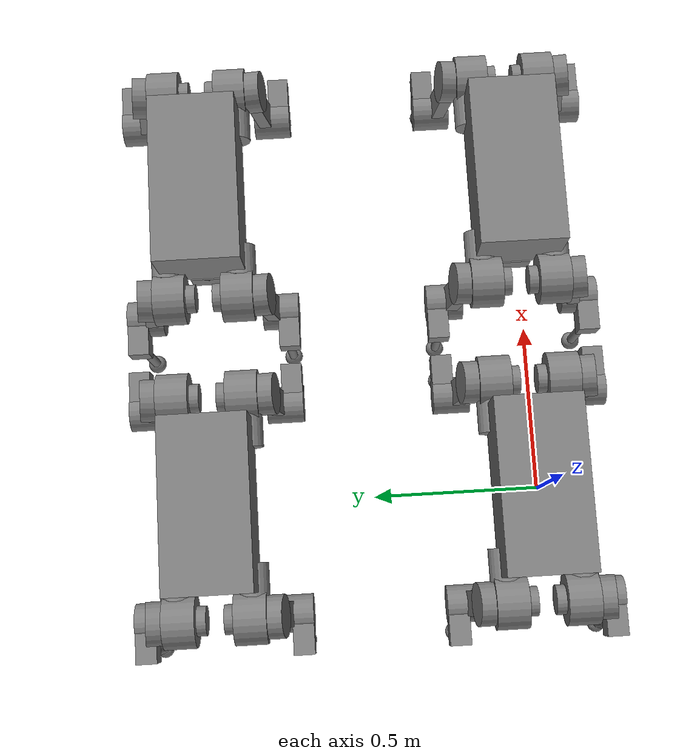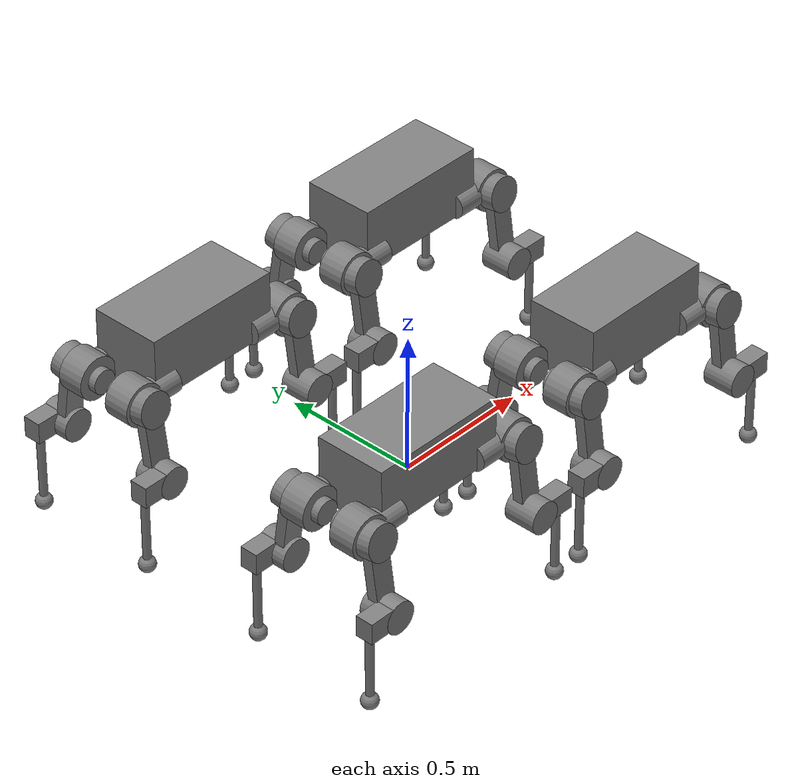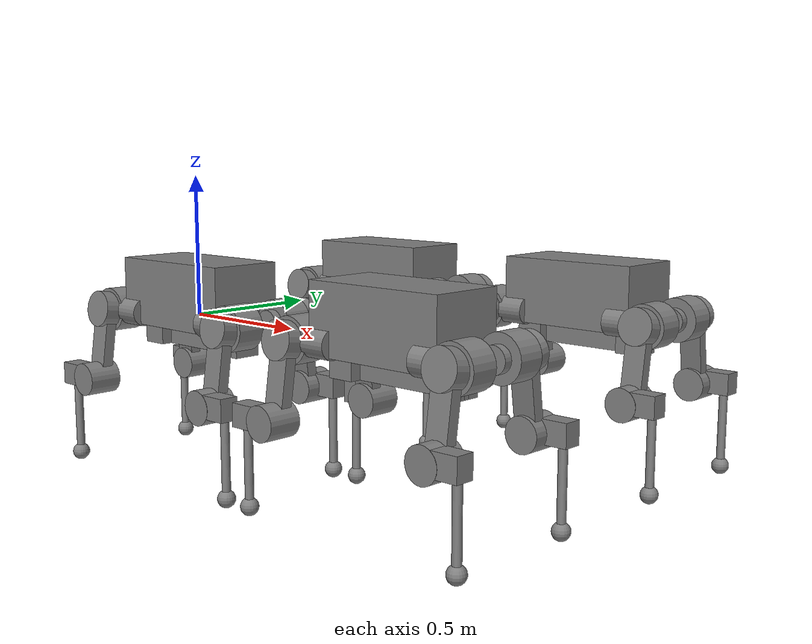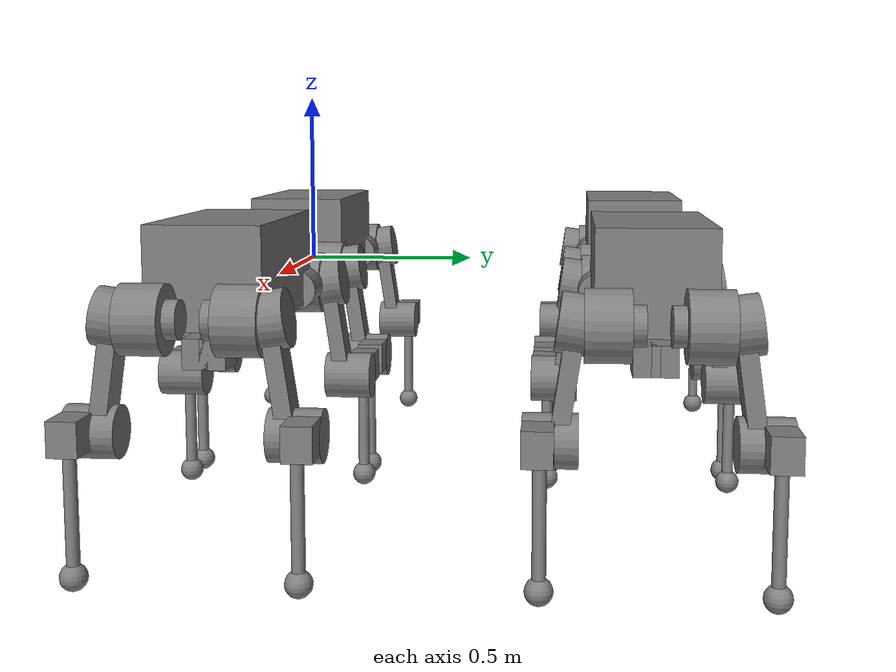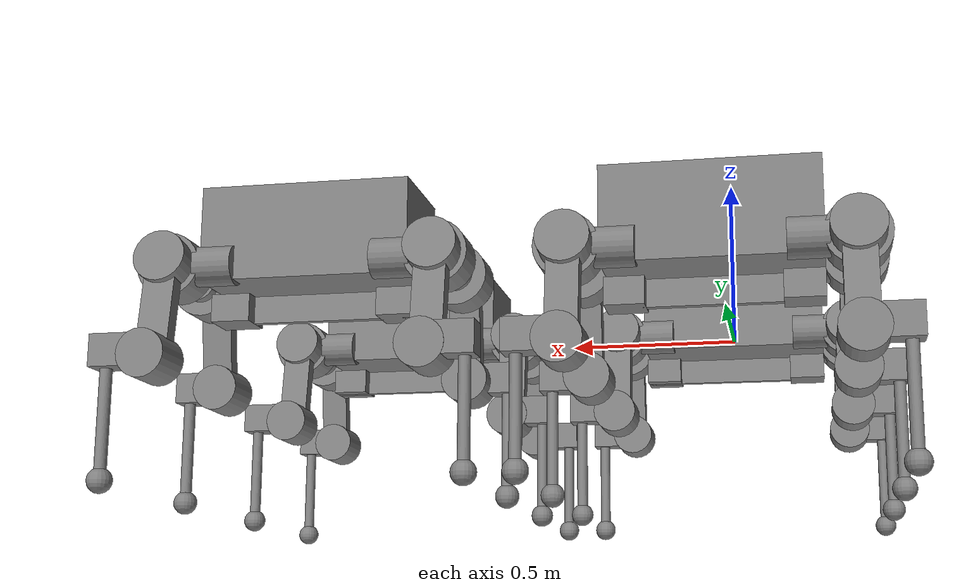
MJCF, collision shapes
<mujoco><compiler angle="radian" meshdir="assets" texturedir="assets" autolimits="true" />

  <option cone="elliptic" impratio="100" />

  <asset>
    <material name="light_gray" rgba="0.8 0.8 0.8 1" />
    <material name="dark_gray" rgba="0.64 0.64 0.64 1" />
    <material name="alu_eloxiert" rgba="0.1139 0.1139 0.1139 1" />
    <material name="any_blau" rgba="0.2399 0.3499 0.5899 1" />
    <texture name="base_uv_texture" type="2d" file="base_uv_texture.png" />
    <material name="carbon_fibre_logo" texture="base_uv_texture" specular="1" shininess="1" />
    <material name="rot_emcy" rgba="0.2611 0.09645 0.0735 1" />
    <material name="yellow_emcy" rgba="0.5987 0.4607 0.2442 1" />
    <material name="copper" rgba="0.8 0.4673 0.284 1" />
    <material name="foam_dark" rgba="0.1 0.1 0.1 1" />
    <texture name="carbon_uv_texture" type="2d" file="carbon_uv_texture.png" />
    <material name="carbon_fibre" texture="carbon_uv_texture" specular="1" shininess="1" />

    <mesh class="anymal_b" file="anymal_base_0.obj" />
    <mesh class="anymal_b" file="anymal_base_1.obj" />
    <mesh class="anymal_b" file="anymal_base_2.obj" />
    <mesh class="anymal_b" file="anymal_base_3.obj" />
    <mesh class="anymal_b" file="anymal_base_4.obj" />
    <mesh class="anymal_b" file="anymal_base_5.obj" />
    <mesh class="anymal_b" file="anymal_base_6.obj" />
    <mesh class="anymal_b" file="anymal_base_7.obj" />
    <mesh class="anymal_b" file="anymal_hip_l_0.obj" />
    <mesh class="anymal_b" file="anymal_hip_l_1.obj" />
    <mesh class="anymal_b" file="anymal_hip_l_2.obj" />
    <mesh class="anymal_b" file="anymal_hip_l_3.obj" />
    <mesh class="anymal_b" file="anymal_hip_l_4.obj" />
    <mesh class="anymal_b" file="anymal_hip_l_5.obj" />
    <mesh class="anymal_b" file="anymal_hip_l_6.obj" />
    <mesh class="anymal_b" file="anymal_thigh_l_0.obj" />
    <mesh class="anymal_b" file="anymal_thigh_l_1.obj" />
    <mesh class="anymal_b" file="anymal_thigh_l_2.obj" />
    <mesh class="anymal_b" file="anymal_thigh_l_3.obj" />
    <mesh class="anymal_b" file="anymal_thigh_l_4.obj" />
    <mesh class="anymal_b" file="anymal_thigh_l_5.obj" />
    <mesh class="anymal_b" file="anymal_shank_l_0.obj" />
    <mesh class="anymal_b" file="anymal_shank_l_1.obj" />
    <mesh class="anymal_b" file="anymal_shank_l_2.obj" />
    <mesh class="anymal_b" file="anymal_shank_l_3.obj" />
    <mesh class="anymal_b" file="anymal_hip_r_0.obj" />
    <mesh class="anymal_b" file="anymal_hip_r_1.obj" />
    <mesh class="anymal_b" file="anymal_hip_r_2.obj" />
    <mesh class="anymal_b" file="anymal_hip_r_3.obj" />
    <mesh class="anymal_b" file="anymal_hip_r_4.obj" />
    <mesh class="anymal_b" file="anymal_hip_r_5.obj" />
    <mesh class="anymal_b" file="anymal_hip_r_6.obj" />
    <mesh class="anymal_b" file="anymal_thigh_r_0.obj" />
    <mesh class="anymal_b" file="anymal_thigh_r_1.obj" />
    <mesh class="anymal_b" file="anymal_thigh_r_2.obj" />
    <mesh class="anymal_b" file="anymal_thigh_r_3.obj" />
    <mesh class="anymal_b" file="anymal_thigh_r_4.obj" />
    <mesh class="anymal_b" file="anymal_thigh_r_5.obj" />
    <mesh class="anymal_b" file="anymal_shank_r_0.obj" />
    <mesh class="anymal_b" file="anymal_shank_r_1.obj" />
    <mesh class="anymal_b" file="anymal_shank_r_2.obj" />
    <mesh class="anymal_b" file="anymal_shank_r_3.obj" />
    <mesh class="anymal_b" file="anymal_foot_0.obj" />
    <mesh class="anymal_b" file="anymal_foot_1.obj" />
    <mesh class="anymal_b" file="anymal_foot_2.obj" />
    <mesh class="anymal_b" file="anymal_foot_3.obj" />
  </asset>

  <worldbody><body name="base_copy_0" pos="0 0 0" quat="0 0 0 1" childclass="anymal_b">
      <freejoint />
      <inertial mass="19.2035" pos="0.0025 0 0.0502071" quat="0.5 0.5 0.5 0.5" diaginertia="0.639559 0.624031 0.217374" />
      <geom class="visual" mesh="anymal_base_0" material="yellow_emcy" />
      <geom class="visual" mesh="anymal_base_1" material="rot_emcy" />
      <geom class="visual" mesh="anymal_base_2" material="dark_gray" />
      <geom class="visual" mesh="anymal_base_3" material="any_blau" />
      <geom class="visual" mesh="anymal_base_4" material="alu_eloxiert" />
      <geom class="visual" mesh="anymal_base_5" material="carbon_fibre_logo" />
      <geom class="visual" mesh="anymal_base_6" material="foam_dark" />
      <geom class="visual" mesh="anymal_base_7" material="light_gray" />
      <geom class="collision" size="0.2655 0.135 0.12" pos="0 0 0.08" type="box" />
      <geom class="haa_actuator" pos="0.227 0.116 0" />
      <geom class="haa_actuator" pos="0.227 -0.116 0" />
      <geom class="haa_actuator" pos="-0.227 0.116 0" />
      <geom class="haa_actuator" pos="-0.227 -0.116 0" />
      <geom class="belly_plate_bump" pos="0.2155 0 -0.09" />
      <geom class="belly_plate_bump" pos="-0.2155 0 -0.09" />
      <geom class="collision" size="0.2655 0.01 0.035" pos="0 0 -0.09" type="box" />
      <body name="LF_HIP_copy_0" pos="0.277 0.116 0">
        <inertial mass="1.42462" pos="0.0645163 -0.0037871 -0.000152184" quat="0.996866 0.0379822 0.0252009 -0.0646548" diaginertia="0.00243341 0.00230249 0.00197758" />
        <joint name="LF_HAA_copy_0" class="HAA" />
        <geom class="visual" mesh="anymal_hip_l_0" material="light_gray" />
        <geom class="visual" mesh="anymal_hip_l_1" material="copper" />
        <geom class="visual" mesh="anymal_hip_l_2" material="foam_dark" />
        <geom class="visual" mesh="anymal_hip_l_3" material="alu_eloxiert" />
        <geom class="visual" mesh="anymal_hip_l_4" material="any_blau" />
        <geom class="visual" mesh="anymal_hip_l_5" material="dark_gray" />
        <geom class="visual" mesh="anymal_hip_l_6" material="light_gray" />
        <geom class="protector" pos="0.0635 -0.009 0" quat="1 1 0 0" />
        <geom class="heatfins" pos="0.0635 -0.074 0" quat="1 1 0 0" />
        <body name="LF_THIGH_copy_0" pos="0.0635 0.041 0">
          <inertial mass="1.63498" pos="-0.00389797 0.0542266 -0.214583" quat="0.74395 -0.0633414 0.0362707 0.664237" diaginertia="0.0122697 0.0120427 0.00228302" />
          <joint name="LF_HFE_copy_0" class="HFE" />
          <geom class="visual" material="any_blau" mesh="anymal_thigh_l_0" />
          <geom class="visual" material="dark_gray" mesh="anymal_thigh_l_1" />
          <geom class="visual" material="copper" mesh="anymal_thigh_l_2" />
          <geom class="visual" material="alu_eloxiert" mesh="anymal_thigh_l_3" />
          <geom class="visual" material="foam_dark" mesh="anymal_thigh_l_4" />
          <geom class="visual" material="light_gray" mesh="anymal_thigh_l_5" />
          <geom class="thigh_with_fins" pos="0 0.035 -0.125" quat="0.997373 0.0724365 0 0" />
          <geom class="kfe_actuator" pos="0 0.069 -0.25" quat="1 1 0 0" />
          <geom class="upper_protector" pos="0 -0.005 0" quat="0.654029 0.75647 0 0" />
          <body name="LF_SHANK_copy_0" pos="0 0.109 -0.25">
            <inertial mass="0.472163" pos="0.0696396 -0.0132494 -0.150905" quat="0.677954 -0.0950614 -0.0578104 0.726636" diaginertia="0.0116034 0.0110666 0.000723761" />
            <joint name="LF_KFE_copy_0" class="KFE" />
            <geom class="visual" material="foam_dark" mesh="anymal_shank_l_0" />
            <geom class="visual" material="dark_gray" mesh="anymal_shank_l_1" />
            <geom class="visual" material="light_gray" mesh="anymal_shank_l_2" />
            <geom class="visual" material="light_gray" mesh="anymal_shank_l_3" />
            <geom class="shank" pos="0.065 -0.015 0.01" quat="1 0 1 0" />
            <geom class="visual" material="carbon_fibre" mesh="anymal_foot_0" pos="0.1 -0.02 0.032" />
            <geom class="visual" material="foam_dark" mesh="anymal_foot_1" pos="0.1 -0.02 0.032" />
            <geom class="visual" material="dark_gray" mesh="anymal_foot_2" pos="0.1 -0.02 0.032" />
            <geom class="visual" material="light_gray" mesh="anymal_foot_3" pos="0.1 -0.02 0.032" />
            <geom class="adapter" pos="0.1 -0.02 -0.160625" />
            <geom class="foot" pos="0.1 -0.02 -0.298" />
          </body>
        </body>
      </body>
      <body name="RF_HIP_copy_0" pos="0.277 -0.116 0">
        <inertial mass="1.42462" pos="0.0645163 0.0037871 -0.000152184" quat="0.996866 -0.0379822 0.0252009 0.0646548" diaginertia="0.00243341 0.00230249 0.00197758" />
        <joint name="RF_HAA_copy_0" class="HAA" />
        <geom class="visual" material="light_gray" mesh="anymal_hip_r_0" />
        <geom class="visual" material="copper" mesh="anymal_hip_r_1" />
        <geom class="visual" material="foam_dark" mesh="anymal_hip_r_2" />
        <geom class="visual" material="alu_eloxiert" mesh="anymal_hip_r_3" />
        <geom class="visual" material="any_blau" mesh="anymal_hip_r_4" />
        <geom class="visual" material="dark_gray" mesh="anymal_hip_r_5" />
        <geom class="visual" material="light_gray" mesh="anymal_hip_r_6" />
        <geom class="protector" pos="0.0635 0.009 0" quat="1 1 0 0" />
        <geom class="heatfins" pos="0.0635 0.074 0" quat="1 1 0 0" />
        <body name="RF_THIGH_copy_0" pos="0.0635 -0.041 0">
          <inertial mass="1.63498" pos="-0.00389797 -0.0542266 -0.214583" quat="0.664237 0.0362707 -0.0633414 0.74395" diaginertia="0.0122697 0.0120427 0.00228302" />
          <joint name="RF_HFE_copy_0" class="HFE" />
          <geom class="visual" material="any_blau" mesh="anymal_thigh_r_0" />
          <geom class="visual" material="dark_gray" mesh="anymal_thigh_r_1" />
          <geom class="visual" material="copper" mesh="anymal_thigh_r_2" />
          <geom class="visual" material="alu_eloxiert" mesh="anymal_thigh_r_3" />
          <geom class="visual" material="foam_dark" mesh="anymal_thigh_r_4" />
          <geom class="visual" material="light_gray" mesh="anymal_thigh_r_5" />
          <geom class="thigh_with_fins" pos="0 -0.035 -0.125" quat="0.997373 -0.0724365 0 0" />
          <geom class="kfe_actuator" pos="0 -0.069 -0.25" quat="1 1 0 0" />
          <geom class="upper_protector" pos="0 0.005 0" quat="0.654029 -0.75647 0 0" />
          <body name="RF_SHANK_copy_0" pos="0 -0.109 -0.25">
            <inertial mass="0.472163" pos="0.0696396 0.0132494 -0.150905" quat="0.726636 -0.0578104 -0.0950614 0.677954" diaginertia="0.0116034 0.0110666 0.000723761" />
            <joint name="RF_KFE_copy_0" class="KFE" />
            <geom class="visual" material="foam_dark" mesh="anymal_shank_r_0" />
            <geom class="visual" material="dark_gray" mesh="anymal_shank_r_1" />
            <geom class="visual" material="light_gray" mesh="anymal_shank_r_2" />
            <geom class="visual" material="light_gray" mesh="anymal_shank_r_3" />
            <geom class="shank" pos="0.065 0.015 0.01" quat="1 0 1 0" />
            <geom class="visual" material="carbon_fibre" mesh="anymal_foot_0" pos="0.1 0.02 0.032" />
            <geom class="visual" material="foam_dark" mesh="anymal_foot_1" pos="0.1 0.02 0.032" />
            <geom class="visual" material="dark_gray" mesh="anymal_foot_2" pos="0.1 0.02 0.032" />
            <geom class="visual" material="light_gray" mesh="anymal_foot_3" pos="0.1 0.02 0.032" />
            <geom class="adapter" pos="0.1 0.02 -0.160625" />
            <geom class="foot" pos="0.1 0.02 -0.298" />
          </body>
        </body>
      </body>
      <body name="LH_HIP_copy_0" pos="-0.277 0.116 0">
        <inertial mass="1.42462" pos="-0.0645163 -0.0037871 -0.000152184" quat="0.996866 0.0379822 -0.0252009 0.0646548" diaginertia="0.00243341 0.00230249 0.00197758" />
        <joint name="LH_HAA_copy_0" class="HAA" />
        <geom class="visual_zflip" material="light_gray" mesh="anymal_hip_r_0" />
        <geom class="visual_zflip" material="copper" mesh="anymal_hip_r_1" />
        <geom class="visual_zflip" material="foam_dark" mesh="anymal_hip_r_2" />
        <geom class="visual_zflip" material="alu_eloxiert" mesh="anymal_hip_r_3" />
        <geom class="visual_zflip" material="any_blau" mesh="anymal_hip_r_4" />
        <geom class="visual_zflip" material="dark_gray" mesh="anymal_hip_r_5" />
        <geom class="visual_zflip" material="light_gray" mesh="anymal_hip_r_6" />
        <geom class="protector" pos="-0.0635 -0.009 0" quat="1 -1 0 0" />
        <geom class="heatfins" pos="-0.0635 -0.074 0" quat="1 -1 0 0" />
        <body name="LH_THIGH_copy_0" pos="-0.0635 0.041 0">
          <inertial mass="1.63498" pos="0.00389797 0.0542266 -0.214583" quat="0.664237 -0.0362707 0.0633414 0.74395" diaginertia="0.0122697 0.0120427 0.00228302" />
          <joint name="LH_HFE_copy_0" class="HFE" />
          <geom class="visual_zflip" material="any_blau" mesh="anymal_thigh_r_0" />
          <geom class="visual_zflip" material="dark_gray" mesh="anymal_thigh_r_1" />
          <geom class="visual_zflip" material="copper" mesh="anymal_thigh_r_2" />
          <geom class="visual_zflip" material="alu_eloxiert" mesh="anymal_thigh_r_3" />
          <geom class="visual_zflip" material="foam_dark" mesh="anymal_thigh_r_4" />
          <geom class="visual_zflip" material="light_gray" mesh="anymal_thigh_r_5" />
          <geom class="thigh_with_fins" pos="0 0.035 -0.125" quat="0.997373 0.0724365 0 0" />
          <geom class="kfe_actuator" pos="0 0.069 -0.25" quat="1 1 0 0" />
          <geom class="upper_protector" pos="0 -0.005 0" quat="0.654029 0.75647 0 0" />
          <body name="LH_SHANK_copy_0" pos="0 0.109 -0.25">
            <inertial mass="0.472163" pos="-0.0696396 -0.0132494 -0.150905" quat="0.726636 0.0578104 0.0950615 0.677954" diaginertia="0.0116034 0.0110666 0.000723761" />
            <joint name="LH_KFE_copy_0" class="KFE" />
            <geom class="visual_zflip" material="foam_dark" mesh="anymal_shank_r_0" />
            <geom class="visual_zflip" material="dark_gray" mesh="anymal_shank_r_1" />
            <geom class="visual_zflip" material="light_gray" mesh="anymal_shank_r_2" />
            <geom class="visual_zflip" material="light_gray" mesh="anymal_shank_r_3" />
            <geom class="shank" pos="-0.065 -0.015 0.01" quat="1 0 1 0" />
            <geom class="visual_zflip" material="carbon_fibre" mesh="anymal_foot_0" pos="-0.1 -0.02 0.032" />
            <geom class="visual_zflip" material="foam_dark" mesh="anymal_foot_1" pos="-0.1 -0.02 0.032" />
            <geom class="visual_zflip" material="dark_gray" mesh="anymal_foot_2" pos="-0.1 -0.02 0.032" />
            <geom class="visual_zflip" material="light_gray" mesh="anymal_foot_3" pos="-0.1 -0.02 0.032" />
            <geom class="adapter" pos="-0.1 -0.02 -0.160625" />
            <geom class="foot" pos="-0.1 -0.02 -0.298" />
          </body>
        </body>
      </body>
      <body name="RH_HIP_copy_0" pos="-0.277 -0.116 0">
        <inertial mass="1.42462" pos="-0.0645163 0.0037871 -0.000152184" quat="0.996866 -0.0379822 -0.0252009 -0.0646548" diaginertia="0.00243341 0.00230249 0.00197758" />
        <joint name="RH_HAA_copy_0" class="HAA" />
        <geom class="visual_zflip" mesh="anymal_hip_l_0" material="light_gray" />
        <geom class="visual_zflip" mesh="anymal_hip_l_1" material="copper" />
        <geom class="visual_zflip" mesh="anymal_hip_l_2" material="foam_dark" />
        <geom class="visual_zflip" mesh="anymal_hip_l_3" material="alu_eloxiert" />
        <geom class="visual_zflip" mesh="anymal_hip_l_4" material="any_blau" />
        <geom class="visual_zflip" mesh="anymal_hip_l_5" material="dark_gray" />
        <geom class="visual_zflip" mesh="anymal_hip_l_6" material="light_gray" />
        <geom class="protector" pos="-0.0635 0.009 0" quat="1 -1 0 0" />
        <geom class="heatfins" pos="-0.0635 0.074 0" quat="1 -1 0 0" />
        <body name="RH_THIGH_copy_0" pos="-0.0635 -0.041 0">
          <inertial mass="1.63498" pos="0.00389797 -0.0542266 -0.214583" quat="0.74395 0.0633414 -0.0362707 0.664237" diaginertia="0.0122697 0.0120427 0.00228302" />
          <joint name="RH_HFE_copy_0" class="HFE" />
          <geom class="visual_zflip" material="any_blau" mesh="anymal_thigh_l_0" />
          <geom class="visual_zflip" material="dark_gray" mesh="anymal_thigh_l_1" />
          <geom class="visual_zflip" material="copper" mesh="anymal_thigh_l_2" />
          <geom class="visual_zflip" material="alu_eloxiert" mesh="anymal_thigh_l_3" />
          <geom class="visual_zflip" material="foam_dark" mesh="anymal_thigh_l_4" />
          <geom class="visual_zflip" material="light_gray" mesh="anymal_thigh_l_5" />
          <geom class="thigh_with_fins" pos="0 -0.035 -0.125" quat="0.997373 -0.0724365 0 0" />
          <geom class="kfe_actuator" pos="0 -0.069 -0.25" quat="1 1 0 0" />
          <geom class="upper_protector" pos="0 0.005 0" quat="0.654029 -0.75647 0 0" />
          <body name="RH_SHANK_copy_0" pos="0 -0.109 -0.25">
            <inertial mass="0.472163" pos="-0.0696396 0.0132494 -0.150905" quat="0.677954 0.0950614 0.0578104 0.726636" diaginertia="0.0116034 0.0110666 0.000723761" />
            <joint name="RH_KFE_copy_0" class="KFE" />
            <geom class="visual_zflip" material="foam_dark" mesh="anymal_shank_l_0" />
            <geom class="visual_zflip" material="dark_gray" mesh="anymal_shank_l_1" />
            <geom class="visual_zflip" material="light_gray" mesh="anymal_shank_l_2" />
            <geom class="visual_zflip" material="light_gray" mesh="anymal_shank_l_3" />
            <geom class="shank" pos="-0.065 0.015 0.01" quat="1 0 1 0" />
            <geom class="visual_zflip" material="carbon_fibre" mesh="anymal_foot_0" pos="-0.1 0.02 0.032" />
            <geom class="visual_zflip" material="foam_dark" mesh="anymal_foot_1" pos="-0.1 0.02 0.032" />
            <geom class="visual_zflip" material="dark_gray" mesh="anymal_foot_2" pos="-0.1 0.02 0.032" />
            <geom class="visual_zflip" material="light_gray" mesh="anymal_foot_3" pos="-0.1 0.02 0.032" />
            <geom class="adapter" pos="-0.1 0.02 -0.160625" />
            <geom class="foot" pos="-0.1 0.02 -0.298" />
          </body>
        </body>
      </body>
    </body>
  <body name="base_copy_1" pos="1 0 0" quat="0 0 0 1" childclass="anymal_b">
      <freejoint />
      <inertial mass="19.2035" pos="0.0025 0 0.0502071" quat="0.5 0.5 0.5 0.5" diaginertia="0.639559 0.624031 0.217374" />
      <geom class="visual" mesh="anymal_base_0" material="yellow_emcy" />
      <geom class="visual" mesh="anymal_base_1" material="rot_emcy" />
      <geom class="visual" mesh="anymal_base_2" material="dark_gray" />
      <geom class="visual" mesh="anymal_base_3" material="any_blau" />
      <geom class="visual" mesh="anymal_base_4" material="alu_eloxiert" />
      <geom class="visual" mesh="anymal_base_5" material="carbon_fibre_logo" />
      <geom class="visual" mesh="anymal_base_6" material="foam_dark" />
      <geom class="visual" mesh="anymal_base_7" material="light_gray" />
      <geom class="collision" size="0.2655 0.135 0.12" pos="0 0 0.08" type="box" />
      <geom class="haa_actuator" pos="0.227 0.116 0" />
      <geom class="haa_actuator" pos="0.227 -0.116 0" />
      <geom class="haa_actuator" pos="-0.227 0.116 0" />
      <geom class="haa_actuator" pos="-0.227 -0.116 0" />
      <geom class="belly_plate_bump" pos="0.2155 0 -0.09" />
      <geom class="belly_plate_bump" pos="-0.2155 0 -0.09" />
      <geom class="collision" size="0.2655 0.01 0.035" pos="0 0 -0.09" type="box" />
      <body name="LF_HIP_copy_1" pos="0.277 0.116 0">
        <inertial mass="1.42462" pos="0.0645163 -0.0037871 -0.000152184" quat="0.996866 0.0379822 0.0252009 -0.0646548" diaginertia="0.00243341 0.00230249 0.00197758" />
        <joint name="LF_HAA_copy_1" class="HAA" />
        <geom class="visual" mesh="anymal_hip_l_0" material="light_gray" />
        <geom class="visual" mesh="anymal_hip_l_1" material="copper" />
        <geom class="visual" mesh="anymal_hip_l_2" material="foam_dark" />
        <geom class="visual" mesh="anymal_hip_l_3" material="alu_eloxiert" />
        <geom class="visual" mesh="anymal_hip_l_4" material="any_blau" />
        <geom class="visual" mesh="anymal_hip_l_5" material="dark_gray" />
        <geom class="visual" mesh="anymal_hip_l_6" material="light_gray" />
        <geom class="protector" pos="0.0635 -0.009 0" quat="1 1 0 0" />
        <geom class="heatfins" pos="0.0635 -0.074 0" quat="1 1 0 0" />
        <body name="LF_THIGH_copy_1" pos="0.0635 0.041 0">
          <inertial mass="1.63498" pos="-0.00389797 0.0542266 -0.214583" quat="0.74395 -0.0633414 0.0362707 0.664237" diaginertia="0.0122697 0.0120427 0.00228302" />
          <joint name="LF_HFE_copy_1" class="HFE" />
          <geom class="visual" material="any_blau" mesh="anymal_thigh_l_0" />
          <geom class="visual" material="dark_gray" mesh="anymal_thigh_l_1" />
          <geom class="visual" material="copper" mesh="anymal_thigh_l_2" />
          <geom class="visual" material="alu_eloxiert" mesh="anymal_thigh_l_3" />
          <geom class="visual" material="foam_dark" mesh="anymal_thigh_l_4" />
          <geom class="visual" material="light_gray" mesh="anymal_thigh_l_5" />
          <geom class="thigh_with_fins" pos="0 0.035 -0.125" quat="0.997373 0.0724365 0 0" />
          <geom class="kfe_actuator" pos="0 0.069 -0.25" quat="1 1 0 0" />
          <geom class="upper_protector" pos="0 -0.005 0" quat="0.654029 0.75647 0 0" />
          <body name="LF_SHANK_copy_1" pos="0 0.109 -0.25">
            <inertial mass="0.472163" pos="0.0696396 -0.0132494 -0.150905" quat="0.677954 -0.0950614 -0.0578104 0.726636" diaginertia="0.0116034 0.0110666 0.000723761" />
            <joint name="LF_KFE_copy_1" class="KFE" />
            <geom class="visual" material="foam_dark" mesh="anymal_shank_l_0" />
            <geom class="visual" material="dark_gray" mesh="anymal_shank_l_1" />
            <geom class="visual" material="light_gray" mesh="anymal_shank_l_2" />
            <geom class="visual" material="light_gray" mesh="anymal_shank_l_3" />
            <geom class="shank" pos="0.065 -0.015 0.01" quat="1 0 1 0" />
            <geom class="visual" material="carbon_fibre" mesh="anymal_foot_0" pos="0.1 -0.02 0.032" />
            <geom class="visual" material="foam_dark" mesh="anymal_foot_1" pos="0.1 -0.02 0.032" />
            <geom class="visual" material="dark_gray" mesh="anymal_foot_2" pos="0.1 -0.02 0.032" />
            <geom class="visual" material="light_gray" mesh="anymal_foot_3" pos="0.1 -0.02 0.032" />
            <geom class="adapter" pos="0.1 -0.02 -0.160625" />
            <geom class="foot" pos="0.1 -0.02 -0.298" />
          </body>
        </body>
      </body>
      <body name="RF_HIP_copy_1" pos="0.277 -0.116 0">
        <inertial mass="1.42462" pos="0.0645163 0.0037871 -0.000152184" quat="0.996866 -0.0379822 0.0252009 0.0646548" diaginertia="0.00243341 0.00230249 0.00197758" />
        <joint name="RF_HAA_copy_1" class="HAA" />
        <geom class="visual" material="light_gray" mesh="anymal_hip_r_0" />
        <geom class="visual" material="copper" mesh="anymal_hip_r_1" />
        <geom class="visual" material="foam_dark" mesh="anymal_hip_r_2" />
        <geom class="visual" material="alu_eloxiert" mesh="anymal_hip_r_3" />
        <geom class="visual" material="any_blau" mesh="anymal_hip_r_4" />
        <geom class="visual" material="dark_gray" mesh="anymal_hip_r_5" />
        <geom class="visual" material="light_gray" mesh="anymal_hip_r_6" />
        <geom class="protector" pos="0.0635 0.009 0" quat="1 1 0 0" />
        <geom class="heatfins" pos="0.0635 0.074 0" quat="1 1 0 0" />
        <body name="RF_THIGH_copy_1" pos="0.0635 -0.041 0">
          <inertial mass="1.63498" pos="-0.00389797 -0.0542266 -0.214583" quat="0.664237 0.0362707 -0.0633414 0.74395" diaginertia="0.0122697 0.0120427 0.00228302" />
          <joint name="RF_HFE_copy_1" class="HFE" />
          <geom class="visual" material="any_blau" mesh="anymal_thigh_r_0" />
          <geom class="visual" material="dark_gray" mesh="anymal_thigh_r_1" />
          <geom class="visual" material="copper" mesh="anymal_thigh_r_2" />
          <geom class="visual" material="alu_eloxiert" mesh="anymal_thigh_r_3" />
          <geom class="visual" material="foam_dark" mesh="anymal_thigh_r_4" />
          <geom class="visual" material="light_gray" mesh="anymal_thigh_r_5" />
          <geom class="thigh_with_fins" pos="0 -0.035 -0.125" quat="0.997373 -0.0724365 0 0" />
          <geom class="kfe_actuator" pos="0 -0.069 -0.25" quat="1 1 0 0" />
          <geom class="upper_protector" pos="0 0.005 0" quat="0.654029 -0.75647 0 0" />
          <body name="RF_SHANK_copy_1" pos="0 -0.109 -0.25">
            <inertial mass="0.472163" pos="0.0696396 0.0132494 -0.150905" quat="0.726636 -0.0578104 -0.0950614 0.677954" diaginertia="0.0116034 0.0110666 0.000723761" />
            <joint name="RF_KFE_copy_1" class="KFE" />
            <geom class="visual" material="foam_dark" mesh="anymal_shank_r_0" />
            <geom class="visual" material="dark_gray" mesh="anymal_shank_r_1" />
            <geom class="visual" material="light_gray" mesh="anymal_shank_r_2" />
            <geom class="visual" material="light_gray" mesh="anymal_shank_r_3" />
            <geom class="shank" pos="0.065 0.015 0.01" quat="1 0 1 0" />
            <geom class="visual" material="carbon_fibre" mesh="anymal_foot_0" pos="0.1 0.02 0.032" />
            <geom class="visual" material="foam_dark" mesh="anymal_foot_1" pos="0.1 0.02 0.032" />
            <geom class="visual" material="dark_gray" mesh="anymal_foot_2" pos="0.1 0.02 0.032" />
            <geom class="visual" material="light_gray" mesh="anymal_foot_3" pos="0.1 0.02 0.032" />
            <geom class="adapter" pos="0.1 0.02 -0.160625" />
            <geom class="foot" pos="0.1 0.02 -0.298" />
          </body>
        </body>
      </body>
      <body name="LH_HIP_copy_1" pos="-0.277 0.116 0">
        <inertial mass="1.42462" pos="-0.0645163 -0.0037871 -0.000152184" quat="0.996866 0.0379822 -0.0252009 0.0646548" diaginertia="0.00243341 0.00230249 0.00197758" />
        <joint name="LH_HAA_copy_1" class="HAA" />
        <geom class="visual_zflip" material="light_gray" mesh="anymal_hip_r_0" />
        <geom class="visual_zflip" material="copper" mesh="anymal_hip_r_1" />
        <geom class="visual_zflip" material="foam_dark" mesh="anymal_hip_r_2" />
        <geom class="visual_zflip" material="alu_eloxiert" mesh="anymal_hip_r_3" />
        <geom class="visual_zflip" material="any_blau" mesh="anymal_hip_r_4" />
        <geom class="visual_zflip" material="dark_gray" mesh="anymal_hip_r_5" />
        <geom class="visual_zflip" material="light_gray" mesh="anymal_hip_r_6" />
        <geom class="protector" pos="-0.0635 -0.009 0" quat="1 -1 0 0" />
        <geom class="heatfins" pos="-0.0635 -0.074 0" quat="1 -1 0 0" />
        <body name="LH_THIGH_copy_1" pos="-0.0635 0.041 0">
          <inertial mass="1.63498" pos="0.00389797 0.0542266 -0.214583" quat="0.664237 -0.0362707 0.0633414 0.74395" diaginertia="0.0122697 0.0120427 0.00228302" />
          <joint name="LH_HFE_copy_1" class="HFE" />
          <geom class="visual_zflip" material="any_blau" mesh="anymal_thigh_r_0" />
          <geom class="visual_zflip" material="dark_gray" mesh="anymal_thigh_r_1" />
          <geom class="visual_zflip" material="copper" mesh="anymal_thigh_r_2" />
          <geom class="visual_zflip" material="alu_eloxiert" mesh="anymal_thigh_r_3" />
          <geom class="visual_zflip" material="foam_dark" mesh="anymal_thigh_r_4" />
          <geom class="visual_zflip" material="light_gray" mesh="anymal_thigh_r_5" />
          <geom class="thigh_with_fins" pos="0 0.035 -0.125" quat="0.997373 0.0724365 0 0" />
          <geom class="kfe_actuator" pos="0 0.069 -0.25" quat="1 1 0 0" />
          <geom class="upper_protector" pos="0 -0.005 0" quat="0.654029 0.75647 0 0" />
          <body name="LH_SHANK_copy_1" pos="0 0.109 -0.25">
            <inertial mass="0.472163" pos="-0.0696396 -0.0132494 -0.150905" quat="0.726636 0.0578104 0.0950615 0.677954" diaginertia="0.0116034 0.0110666 0.000723761" />
            <joint name="LH_KFE_copy_1" class="KFE" />
            <geom class="visual_zflip" material="foam_dark" mesh="anymal_shank_r_0" />
            <geom class="visual_zflip" material="dark_gray" mesh="anymal_shank_r_1" />
            <geom class="visual_zflip" material="light_gray" mesh="anymal_shank_r_2" />
            <geom class="visual_zflip" material="light_gray" mesh="anymal_shank_r_3" />
            <geom class="shank" pos="-0.065 -0.015 0.01" quat="1 0 1 0" />
            <geom class="visual_zflip" material="carbon_fibre" mesh="anymal_foot_0" pos="-0.1 -0.02 0.032" />
            <geom class="visual_zflip" material="foam_dark" mesh="anymal_foot_1" pos="-0.1 -0.02 0.032" />
            <geom class="visual_zflip" material="dark_gray" mesh="anymal_foot_2" pos="-0.1 -0.02 0.032" />
            <geom class="visual_zflip" material="light_gray" mesh="anymal_foot_3" pos="-0.1 -0.02 0.032" />
            <geom class="adapter" pos="-0.1 -0.02 -0.160625" />
            <geom class="foot" pos="-0.1 -0.02 -0.298" />
          </body>
        </body>
      </body>
      <body name="RH_HIP_copy_1" pos="-0.277 -0.116 0">
        <inertial mass="1.42462" pos="-0.0645163 0.0037871 -0.000152184" quat="0.996866 -0.0379822 -0.0252009 -0.0646548" diaginertia="0.00243341 0.00230249 0.00197758" />
        <joint name="RH_HAA_copy_1" class="HAA" />
        <geom class="visual_zflip" mesh="anymal_hip_l_0" material="light_gray" />
        <geom class="visual_zflip" mesh="anymal_hip_l_1" material="copper" />
        <geom class="visual_zflip" mesh="anymal_hip_l_2" material="foam_dark" />
        <geom class="visual_zflip" mesh="anymal_hip_l_3" material="alu_eloxiert" />
        <geom class="visual_zflip" mesh="anymal_hip_l_4" material="any_blau" />
        <geom class="visual_zflip" mesh="anymal_hip_l_5" material="dark_gray" />
        <geom class="visual_zflip" mesh="anymal_hip_l_6" material="light_gray" />
        <geom class="protector" pos="-0.0635 0.009 0" quat="1 -1 0 0" />
        <geom class="heatfins" pos="-0.0635 0.074 0" quat="1 -1 0 0" />
        <body name="RH_THIGH_copy_1" pos="-0.0635 -0.041 0">
          <inertial mass="1.63498" pos="0.00389797 -0.0542266 -0.214583" quat="0.74395 0.0633414 -0.0362707 0.664237" diaginertia="0.0122697 0.0120427 0.00228302" />
          <joint name="RH_HFE_copy_1" class="HFE" />
          <geom class="visual_zflip" material="any_blau" mesh="anymal_thigh_l_0" />
          <geom class="visual_zflip" material="dark_gray" mesh="anymal_thigh_l_1" />
          <geom class="visual_zflip" material="copper" mesh="anymal_thigh_l_2" />
          <geom class="visual_zflip" material="alu_eloxiert" mesh="anymal_thigh_l_3" />
          <geom class="visual_zflip" material="foam_dark" mesh="anymal_thigh_l_4" />
          <geom class="visual_zflip" material="light_gray" mesh="anymal_thigh_l_5" />
          <geom class="thigh_with_fins" pos="0 -0.035 -0.125" quat="0.997373 -0.0724365 0 0" />
          <geom class="kfe_actuator" pos="0 -0.069 -0.25" quat="1 1 0 0" />
          <geom class="upper_protector" pos="0 0.005 0" quat="0.654029 -0.75647 0 0" />
          <body name="RH_SHANK_copy_1" pos="0 -0.109 -0.25">
            <inertial mass="0.472163" pos="-0.0696396 0.0132494 -0.150905" quat="0.677954 0.0950614 0.0578104 0.726636" diaginertia="0.0116034 0.0110666 0.000723761" />
            <joint name="RH_KFE_copy_1" class="KFE" />
            <geom class="visual_zflip" material="foam_dark" mesh="anymal_shank_l_0" />
            <geom class="visual_zflip" material="dark_gray" mesh="anymal_shank_l_1" />
            <geom class="visual_zflip" material="light_gray" mesh="anymal_shank_l_2" />
            <geom class="visual_zflip" material="light_gray" mesh="anymal_shank_l_3" />
            <geom class="shank" pos="-0.065 0.015 0.01" quat="1 0 1 0" />
            <geom class="visual_zflip" material="carbon_fibre" mesh="anymal_foot_0" pos="-0.1 0.02 0.032" />
            <geom class="visual_zflip" material="foam_dark" mesh="anymal_foot_1" pos="-0.1 0.02 0.032" />
            <geom class="visual_zflip" material="dark_gray" mesh="anymal_foot_2" pos="-0.1 0.02 0.032" />
            <geom class="visual_zflip" material="light_gray" mesh="anymal_foot_3" pos="-0.1 0.02 0.032" />
            <geom class="adapter" pos="-0.1 0.02 -0.160625" />
            <geom class="foot" pos="-0.1 0.02 -0.298" />
          </body>
        </body>
      </body>
    </body>
  <body name="base_copy_2" pos="1 1 0" quat="0 0 0 1" childclass="anymal_b">
      <freejoint />
      <inertial mass="19.2035" pos="0.0025 0 0.0502071" quat="0.5 0.5 0.5 0.5" diaginertia="0.639559 0.624031 0.217374" />
      <geom class="visual" mesh="anymal_base_0" material="yellow_emcy" />
      <geom class="visual" mesh="anymal_base_1" material="rot_emcy" />
      <geom class="visual" mesh="anymal_base_2" material="dark_gray" />
      <geom class="visual" mesh="anymal_base_3" material="any_blau" />
      <geom class="visual" mesh="anymal_base_4" material="alu_eloxiert" />
      <geom class="visual" mesh="anymal_base_5" material="carbon_fibre_logo" />
      <geom class="visual" mesh="anymal_base_6" material="foam_dark" />
      <geom class="visual" mesh="anymal_base_7" material="light_gray" />
      <geom class="collision" size="0.2655 0.135 0.12" pos="0 0 0.08" type="box" />
      <geom class="haa_actuator" pos="0.227 0.116 0" />
      <geom class="haa_actuator" pos="0.227 -0.116 0" />
      <geom class="haa_actuator" pos="-0.227 0.116 0" />
      <geom class="haa_actuator" pos="-0.227 -0.116 0" />
      <geom class="belly_plate_bump" pos="0.2155 0 -0.09" />
      <geom class="belly_plate_bump" pos="-0.2155 0 -0.09" />
      <geom class="collision" size="0.2655 0.01 0.035" pos="0 0 -0.09" type="box" />
      <body name="LF_HIP_copy_2" pos="0.277 0.116 0">
        <inertial mass="1.42462" pos="0.0645163 -0.0037871 -0.000152184" quat="0.996866 0.0379822 0.0252009 -0.0646548" diaginertia="0.00243341 0.00230249 0.00197758" />
        <joint name="LF_HAA_copy_2" class="HAA" />
        <geom class="visual" mesh="anymal_hip_l_0" material="light_gray" />
        <geom class="visual" mesh="anymal_hip_l_1" material="copper" />
        <geom class="visual" mesh="anymal_hip_l_2" material="foam_dark" />
        <geom class="visual" mesh="anymal_hip_l_3" material="alu_eloxiert" />
        <geom class="visual" mesh="anymal_hip_l_4" material="any_blau" />
        <geom class="visual" mesh="anymal_hip_l_5" material="dark_gray" />
        <geom class="visual" mesh="anymal_hip_l_6" material="light_gray" />
        <geom class="protector" pos="0.0635 -0.009 0" quat="1 1 0 0" />
        <geom class="heatfins" pos="0.0635 -0.074 0" quat="1 1 0 0" />
        <body name="LF_THIGH_copy_2" pos="0.0635 0.041 0">
          <inertial mass="1.63498" pos="-0.00389797 0.0542266 -0.214583" quat="0.74395 -0.0633414 0.0362707 0.664237" diaginertia="0.0122697 0.0120427 0.00228302" />
          <joint name="LF_HFE_copy_2" class="HFE" />
          <geom class="visual" material="any_blau" mesh="anymal_thigh_l_0" />
          <geom class="visual" material="dark_gray" mesh="anymal_thigh_l_1" />
          <geom class="visual" material="copper" mesh="anymal_thigh_l_2" />
          <geom class="visual" material="alu_eloxiert" mesh="anymal_thigh_l_3" />
          <geom class="visual" material="foam_dark" mesh="anymal_thigh_l_4" />
          <geom class="visual" material="light_gray" mesh="anymal_thigh_l_5" />
          <geom class="thigh_with_fins" pos="0 0.035 -0.125" quat="0.997373 0.0724365 0 0" />
          <geom class="kfe_actuator" pos="0 0.069 -0.25" quat="1 1 0 0" />
          <geom class="upper_protector" pos="0 -0.005 0" quat="0.654029 0.75647 0 0" />
          <body name="LF_SHANK_copy_2" pos="0 0.109 -0.25">
            <inertial mass="0.472163" pos="0.0696396 -0.0132494 -0.150905" quat="0.677954 -0.0950614 -0.0578104 0.726636" diaginertia="0.0116034 0.0110666 0.000723761" />
            <joint name="LF_KFE_copy_2" class="KFE" />
            <geom class="visual" material="foam_dark" mesh="anymal_shank_l_0" />
            <geom class="visual" material="dark_gray" mesh="anymal_shank_l_1" />
            <geom class="visual" material="light_gray" mesh="anymal_shank_l_2" />
            <geom class="visual" material="light_gray" mesh="anymal_shank_l_3" />
            <geom class="shank" pos="0.065 -0.015 0.01" quat="1 0 1 0" />
            <geom class="visual" material="carbon_fibre" mesh="anymal_foot_0" pos="0.1 -0.02 0.032" />
            <geom class="visual" material="foam_dark" mesh="anymal_foot_1" pos="0.1 -0.02 0.032" />
            <geom class="visual" material="dark_gray" mesh="anymal_foot_2" pos="0.1 -0.02 0.032" />
            <geom class="visual" material="light_gray" mesh="anymal_foot_3" pos="0.1 -0.02 0.032" />
            <geom class="adapter" pos="0.1 -0.02 -0.160625" />
            <geom class="foot" pos="0.1 -0.02 -0.298" />
          </body>
        </body>
      </body>
      <body name="RF_HIP_copy_2" pos="0.277 -0.116 0">
        <inertial mass="1.42462" pos="0.0645163 0.0037871 -0.000152184" quat="0.996866 -0.0379822 0.0252009 0.0646548" diaginertia="0.00243341 0.00230249 0.00197758" />
        <joint name="RF_HAA_copy_2" class="HAA" />
        <geom class="visual" material="light_gray" mesh="anymal_hip_r_0" />
        <geom class="visual" material="copper" mesh="anymal_hip_r_1" />
        <geom class="visual" material="foam_dark" mesh="anymal_hip_r_2" />
        <geom class="visual" material="alu_eloxiert" mesh="anymal_hip_r_3" />
        <geom class="visual" material="any_blau" mesh="anymal_hip_r_4" />
        <geom class="visual" material="dark_gray" mesh="anymal_hip_r_5" />
        <geom class="visual" material="light_gray" mesh="anymal_hip_r_6" />
        <geom class="protector" pos="0.0635 0.009 0" quat="1 1 0 0" />
        <geom class="heatfins" pos="0.0635 0.074 0" quat="1 1 0 0" />
        <body name="RF_THIGH_copy_2" pos="0.0635 -0.041 0">
          <inertial mass="1.63498" pos="-0.00389797 -0.0542266 -0.214583" quat="0.664237 0.0362707 -0.0633414 0.74395" diaginertia="0.0122697 0.0120427 0.00228302" />
          <joint name="RF_HFE_copy_2" class="HFE" />
          <geom class="visual" material="any_blau" mesh="anymal_thigh_r_0" />
          <geom class="visual" material="dark_gray" mesh="anymal_thigh_r_1" />
          <geom class="visual" material="copper" mesh="anymal_thigh_r_2" />
          <geom class="visual" material="alu_eloxiert" mesh="anymal_thigh_r_3" />
          <geom class="visual" material="foam_dark" mesh="anymal_thigh_r_4" />
          <geom class="visual" material="light_gray" mesh="anymal_thigh_r_5" />
          <geom class="thigh_with_fins" pos="0 -0.035 -0.125" quat="0.997373 -0.0724365 0 0" />
          <geom class="kfe_actuator" pos="0 -0.069 -0.25" quat="1 1 0 0" />
          <geom class="upper_protector" pos="0 0.005 0" quat="0.654029 -0.75647 0 0" />
          <body name="RF_SHANK_copy_2" pos="0 -0.109 -0.25">
            <inertial mass="0.472163" pos="0.0696396 0.0132494 -0.150905" quat="0.726636 -0.0578104 -0.0950614 0.677954" diaginertia="0.0116034 0.0110666 0.000723761" />
            <joint name="RF_KFE_copy_2" class="KFE" />
            <geom class="visual" material="foam_dark" mesh="anymal_shank_r_0" />
            <geom class="visual" material="dark_gray" mesh="anymal_shank_r_1" />
            <geom class="visual" material="light_gray" mesh="anymal_shank_r_2" />
            <geom class="visual" material="light_gray" mesh="anymal_shank_r_3" />
            <geom class="shank" pos="0.065 0.015 0.01" quat="1 0 1 0" />
            <geom class="visual" material="carbon_fibre" mesh="anymal_foot_0" pos="0.1 0.02 0.032" />
            <geom class="visual" material="foam_dark" mesh="anymal_foot_1" pos="0.1 0.02 0.032" />
            <geom class="visual" material="dark_gray" mesh="anymal_foot_2" pos="0.1 0.02 0.032" />
            <geom class="visual" material="light_gray" mesh="anymal_foot_3" pos="0.1 0.02 0.032" />
            <geom class="adapter" pos="0.1 0.02 -0.160625" />
            <geom class="foot" pos="0.1 0.02 -0.298" />
          </body>
        </body>
      </body>
      <body name="LH_HIP_copy_2" pos="-0.277 0.116 0">
        <inertial mass="1.42462" pos="-0.0645163 -0.0037871 -0.000152184" quat="0.996866 0.0379822 -0.0252009 0.0646548" diaginertia="0.00243341 0.00230249 0.00197758" />
        <joint name="LH_HAA_copy_2" class="HAA" />
        <geom class="visual_zflip" material="light_gray" mesh="anymal_hip_r_0" />
        <geom class="visual_zflip" material="copper" mesh="anymal_hip_r_1" />
        <geom class="visual_zflip" material="foam_dark" mesh="anymal_hip_r_2" />
        <geom class="visual_zflip" material="alu_eloxiert" mesh="anymal_hip_r_3" />
        <geom class="visual_zflip" material="any_blau" mesh="anymal_hip_r_4" />
        <geom class="visual_zflip" material="dark_gray" mesh="anymal_hip_r_5" />
        <geom class="visual_zflip" material="light_gray" mesh="anymal_hip_r_6" />
        <geom class="protector" pos="-0.0635 -0.009 0" quat="1 -1 0 0" />
        <geom class="heatfins" pos="-0.0635 -0.074 0" quat="1 -1 0 0" />
        <body name="LH_THIGH_copy_2" pos="-0.0635 0.041 0">
          <inertial mass="1.63498" pos="0.00389797 0.0542266 -0.214583" quat="0.664237 -0.0362707 0.0633414 0.74395" diaginertia="0.0122697 0.0120427 0.00228302" />
          <joint name="LH_HFE_copy_2" class="HFE" />
          <geom class="visual_zflip" material="any_blau" mesh="anymal_thigh_r_0" />
          <geom class="visual_zflip" material="dark_gray" mesh="anymal_thigh_r_1" />
          <geom class="visual_zflip" material="copper" mesh="anymal_thigh_r_2" />
          <geom class="visual_zflip" material="alu_eloxiert" mesh="anymal_thigh_r_3" />
          <geom class="visual_zflip" material="foam_dark" mesh="anymal_thigh_r_4" />
          <geom class="visual_zflip" material="light_gray" mesh="anymal_thigh_r_5" />
          <geom class="thigh_with_fins" pos="0 0.035 -0.125" quat="0.997373 0.0724365 0 0" />
          <geom class="kfe_actuator" pos="0 0.069 -0.25" quat="1 1 0 0" />
          <geom class="upper_protector" pos="0 -0.005 0" quat="0.654029 0.75647 0 0" />
          <body name="LH_SHANK_copy_2" pos="0 0.109 -0.25">
            <inertial mass="0.472163" pos="-0.0696396 -0.0132494 -0.150905" quat="0.726636 0.0578104 0.0950615 0.677954" diaginertia="0.0116034 0.0110666 0.000723761" />
            <joint name="LH_KFE_copy_2" class="KFE" />
            <geom class="visual_zflip" material="foam_dark" mesh="anymal_shank_r_0" />
            <geom class="visual_zflip" material="dark_gray" mesh="anymal_shank_r_1" />
            <geom class="visual_zflip" material="light_gray" mesh="anymal_shank_r_2" />
            <geom class="visual_zflip" material="light_gray" mesh="anymal_shank_r_3" />
            <geom class="shank" pos="-0.065 -0.015 0.01" quat="1 0 1 0" />
            <geom class="visual_zflip" material="carbon_fibre" mesh="anymal_foot_0" pos="-0.1 -0.02 0.032" />
            <geom class="visual_zflip" material="foam_dark" mesh="anymal_foot_1" pos="-0.1 -0.02 0.032" />
            <geom class="visual_zflip" material="dark_gray" mesh="anymal_foot_2" pos="-0.1 -0.02 0.032" />
            <geom class="visual_zflip" material="light_gray" mesh="anymal_foot_3" pos="-0.1 -0.02 0.032" />
            <geom class="adapter" pos="-0.1 -0.02 -0.160625" />
            <geom class="foot" pos="-0.1 -0.02 -0.298" />
          </body>
        </body>
      </body>
      <body name="RH_HIP_copy_2" pos="-0.277 -0.116 0">
        <inertial mass="1.42462" pos="-0.0645163 0.0037871 -0.000152184" quat="0.996866 -0.0379822 -0.0252009 -0.0646548" diaginertia="0.00243341 0.00230249 0.00197758" />
        <joint name="RH_HAA_copy_2" class="HAA" />
        <geom class="visual_zflip" mesh="anymal_hip_l_0" material="light_gray" />
        <geom class="visual_zflip" mesh="anymal_hip_l_1" material="copper" />
        <geom class="visual_zflip" mesh="anymal_hip_l_2" material="foam_dark" />
        <geom class="visual_zflip" mesh="anymal_hip_l_3" material="alu_eloxiert" />
        <geom class="visual_zflip" mesh="anymal_hip_l_4" material="any_blau" />
        <geom class="visual_zflip" mesh="anymal_hip_l_5" material="dark_gray" />
        <geom class="visual_zflip" mesh="anymal_hip_l_6" material="light_gray" />
        <geom class="protector" pos="-0.0635 0.009 0" quat="1 -1 0 0" />
        <geom class="heatfins" pos="-0.0635 0.074 0" quat="1 -1 0 0" />
        <body name="RH_THIGH_copy_2" pos="-0.0635 -0.041 0">
          <inertial mass="1.63498" pos="0.00389797 -0.0542266 -0.214583" quat="0.74395 0.0633414 -0.0362707 0.664237" diaginertia="0.0122697 0.0120427 0.00228302" />
          <joint name="RH_HFE_copy_2" class="HFE" />
          <geom class="visual_zflip" material="any_blau" mesh="anymal_thigh_l_0" />
          <geom class="visual_zflip" material="dark_gray" mesh="anymal_thigh_l_1" />
          <geom class="visual_zflip" material="copper" mesh="anymal_thigh_l_2" />
          <geom class="visual_zflip" material="alu_eloxiert" mesh="anymal_thigh_l_3" />
          <geom class="visual_zflip" material="foam_dark" mesh="anymal_thigh_l_4" />
          <geom class="visual_zflip" material="light_gray" mesh="anymal_thigh_l_5" />
          <geom class="thigh_with_fins" pos="0 -0.035 -0.125" quat="0.997373 -0.0724365 0 0" />
          <geom class="kfe_actuator" pos="0 -0.069 -0.25" quat="1 1 0 0" />
          <geom class="upper_protector" pos="0 0.005 0" quat="0.654029 -0.75647 0 0" />
          <body name="RH_SHANK_copy_2" pos="0 -0.109 -0.25">
            <inertial mass="0.472163" pos="-0.0696396 0.0132494 -0.150905" quat="0.677954 0.0950614 0.0578104 0.726636" diaginertia="0.0116034 0.0110666 0.000723761" />
            <joint name="RH_KFE_copy_2" class="KFE" />
            <geom class="visual_zflip" material="foam_dark" mesh="anymal_shank_l_0" />
            <geom class="visual_zflip" material="dark_gray" mesh="anymal_shank_l_1" />
            <geom class="visual_zflip" material="light_gray" mesh="anymal_shank_l_2" />
            <geom class="visual_zflip" material="light_gray" mesh="anymal_shank_l_3" />
            <geom class="shank" pos="-0.065 0.015 0.01" quat="1 0 1 0" />
            <geom class="visual_zflip" material="carbon_fibre" mesh="anymal_foot_0" pos="-0.1 0.02 0.032" />
            <geom class="visual_zflip" material="foam_dark" mesh="anymal_foot_1" pos="-0.1 0.02 0.032" />
            <geom class="visual_zflip" material="dark_gray" mesh="anymal_foot_2" pos="-0.1 0.02 0.032" />
            <geom class="visual_zflip" material="light_gray" mesh="anymal_foot_3" pos="-0.1 0.02 0.032" />
            <geom class="adapter" pos="-0.1 0.02 -0.160625" />
            <geom class="foot" pos="-0.1 0.02 -0.298" />
          </body>
        </body>
      </body>
    </body>
  <body name="base_copy_3" pos="0 1 0" quat="0 0 0 1" childclass="anymal_b">
      <freejoint />
      <inertial mass="19.2035" pos="0.0025 0 0.0502071" quat="0.5 0.5 0.5 0.5" diaginertia="0.639559 0.624031 0.217374" />
      <geom class="visual" mesh="anymal_base_0" material="yellow_emcy" />
      <geom class="visual" mesh="anymal_base_1" material="rot_emcy" />
      <geom class="visual" mesh="anymal_base_2" material="dark_gray" />
      <geom class="visual" mesh="anymal_base_3" material="any_blau" />
      <geom class="visual" mesh="anymal_base_4" material="alu_eloxiert" />
      <geom class="visual" mesh="anymal_base_5" material="carbon_fibre_logo" />
      <geom class="visual" mesh="anymal_base_6" material="foam_dark" />
      <geom class="visual" mesh="anymal_base_7" material="light_gray" />
      <geom class="collision" size="0.2655 0.135 0.12" pos="0 0 0.08" type="box" />
      <geom class="haa_actuator" pos="0.227 0.116 0" />
      <geom class="haa_actuator" pos="0.227 -0.116 0" />
      <geom class="haa_actuator" pos="-0.227 0.116 0" />
      <geom class="haa_actuator" pos="-0.227 -0.116 0" />
      <geom class="belly_plate_bump" pos="0.2155 0 -0.09" />
      <geom class="belly_plate_bump" pos="-0.2155 0 -0.09" />
      <geom class="collision" size="0.2655 0.01 0.035" pos="0 0 -0.09" type="box" />
      <body name="LF_HIP_copy_3" pos="0.277 0.116 0">
        <inertial mass="1.42462" pos="0.0645163 -0.0037871 -0.000152184" quat="0.996866 0.0379822 0.0252009 -0.0646548" diaginertia="0.00243341 0.00230249 0.00197758" />
        <joint name="LF_HAA_copy_3" class="HAA" />
        <geom class="visual" mesh="anymal_hip_l_0" material="light_gray" />
        <geom class="visual" mesh="anymal_hip_l_1" material="copper" />
        <geom class="visual" mesh="anymal_hip_l_2" material="foam_dark" />
        <geom class="visual" mesh="anymal_hip_l_3" material="alu_eloxiert" />
        <geom class="visual" mesh="anymal_hip_l_4" material="any_blau" />
        <geom class="visual" mesh="anymal_hip_l_5" material="dark_gray" />
        <geom class="visual" mesh="anymal_hip_l_6" material="light_gray" />
        <geom class="protector" pos="0.0635 -0.009 0" quat="1 1 0 0" />
        <geom class="heatfins" pos="0.0635 -0.074 0" quat="1 1 0 0" />
        <body name="LF_THIGH_copy_3" pos="0.0635 0.041 0">
          <inertial mass="1.63498" pos="-0.00389797 0.0542266 -0.214583" quat="0.74395 -0.0633414 0.0362707 0.664237" diaginertia="0.0122697 0.0120427 0.00228302" />
          <joint name="LF_HFE_copy_3" class="HFE" />
          <geom class="visual" material="any_blau" mesh="anymal_thigh_l_0" />
          <geom class="visual" material="dark_gray" mesh="anymal_thigh_l_1" />
          <geom class="visual" material="copper" mesh="anymal_thigh_l_2" />
          <geom class="visual" material="alu_eloxiert" mesh="anymal_thigh_l_3" />
          <geom class="visual" material="foam_dark" mesh="anymal_thigh_l_4" />
          <geom class="visual" material="light_gray" mesh="anymal_thigh_l_5" />
          <geom class="thigh_with_fins" pos="0 0.035 -0.125" quat="0.997373 0.0724365 0 0" />
          <geom class="kfe_actuator" pos="0 0.069 -0.25" quat="1 1 0 0" />
          <geom class="upper_protector" pos="0 -0.005 0" quat="0.654029 0.75647 0 0" />
          <body name="LF_SHANK_copy_3" pos="0 0.109 -0.25">
            <inertial mass="0.472163" pos="0.0696396 -0.0132494 -0.150905" quat="0.677954 -0.0950614 -0.0578104 0.726636" diaginertia="0.0116034 0.0110666 0.000723761" />
            <joint name="LF_KFE_copy_3" class="KFE" />
            <geom class="visual" material="foam_dark" mesh="anymal_shank_l_0" />
            <geom class="visual" material="dark_gray" mesh="anymal_shank_l_1" />
            <geom class="visual" material="light_gray" mesh="anymal_shank_l_2" />
            <geom class="visual" material="light_gray" mesh="anymal_shank_l_3" />
            <geom class="shank" pos="0.065 -0.015 0.01" quat="1 0 1 0" />
            <geom class="visual" material="carbon_fibre" mesh="anymal_foot_0" pos="0.1 -0.02 0.032" />
            <geom class="visual" material="foam_dark" mesh="anymal_foot_1" pos="0.1 -0.02 0.032" />
            <geom class="visual" material="dark_gray" mesh="anymal_foot_2" pos="0.1 -0.02 0.032" />
            <geom class="visual" material="light_gray" mesh="anymal_foot_3" pos="0.1 -0.02 0.032" />
            <geom class="adapter" pos="0.1 -0.02 -0.160625" />
            <geom class="foot" pos="0.1 -0.02 -0.298" />
          </body>
        </body>
      </body>
      <body name="RF_HIP_copy_3" pos="0.277 -0.116 0">
        <inertial mass="1.42462" pos="0.0645163 0.0037871 -0.000152184" quat="0.996866 -0.0379822 0.0252009 0.0646548" diaginertia="0.00243341 0.00230249 0.00197758" />
        <joint name="RF_HAA_copy_3" class="HAA" />
        <geom class="visual" material="light_gray" mesh="anymal_hip_r_0" />
        <geom class="visual" material="copper" mesh="anymal_hip_r_1" />
        <geom class="visual" material="foam_dark" mesh="anymal_hip_r_2" />
        <geom class="visual" material="alu_eloxiert" mesh="anymal_hip_r_3" />
        <geom class="visual" material="any_blau" mesh="anymal_hip_r_4" />
        <geom class="visual" material="dark_gray" mesh="anymal_hip_r_5" />
        <geom class="visual" material="light_gray" mesh="anymal_hip_r_6" />
        <geom class="protector" pos="0.0635 0.009 0" quat="1 1 0 0" />
        <geom class="heatfins" pos="0.0635 0.074 0" quat="1 1 0 0" />
        <body name="RF_THIGH_copy_3" pos="0.0635 -0.041 0">
          <inertial mass="1.63498" pos="-0.00389797 -0.0542266 -0.214583" quat="0.664237 0.0362707 -0.0633414 0.74395" diaginertia="0.0122697 0.0120427 0.00228302" />
          <joint name="RF_HFE_copy_3" class="HFE" />
          <geom class="visual" material="any_blau" mesh="anymal_thigh_r_0" />
          <geom class="visual" material="dark_gray" mesh="anymal_thigh_r_1" />
          <geom class="visual" material="copper" mesh="anymal_thigh_r_2" />
          <geom class="visual" material="alu_eloxiert" mesh="anymal_thigh_r_3" />
          <geom class="visual" material="foam_dark" mesh="anymal_thigh_r_4" />
          <geom class="visual" material="light_gray" mesh="anymal_thigh_r_5" />
          <geom class="thigh_with_fins" pos="0 -0.035 -0.125" quat="0.997373 -0.0724365 0 0" />
          <geom class="kfe_actuator" pos="0 -0.069 -0.25" quat="1 1 0 0" />
          <geom class="upper_protector" pos="0 0.005 0" quat="0.654029 -0.75647 0 0" />
          <body name="RF_SHANK_copy_3" pos="0 -0.109 -0.25">
            <inertial mass="0.472163" pos="0.0696396 0.0132494 -0.150905" quat="0.726636 -0.0578104 -0.0950614 0.677954" diaginertia="0.0116034 0.0110666 0.000723761" />
            <joint name="RF_KFE_copy_3" class="KFE" />
            <geom class="visual" material="foam_dark" mesh="anymal_shank_r_0" />
            <geom class="visual" material="dark_gray" mesh="anymal_shank_r_1" />
            <geom class="visual" material="light_gray" mesh="anymal_shank_r_2" />
            <geom class="visual" material="light_gray" mesh="anymal_shank_r_3" />
            <geom class="shank" pos="0.065 0.015 0.01" quat="1 0 1 0" />
            <geom class="visual" material="carbon_fibre" mesh="anymal_foot_0" pos="0.1 0.02 0.032" />
            <geom class="visual" material="foam_dark" mesh="anymal_foot_1" pos="0.1 0.02 0.032" />
            <geom class="visual" material="dark_gray" mesh="anymal_foot_2" pos="0.1 0.02 0.032" />
            <geom class="visual" material="light_gray" mesh="anymal_foot_3" pos="0.1 0.02 0.032" />
            <geom class="adapter" pos="0.1 0.02 -0.160625" />
            <geom class="foot" pos="0.1 0.02 -0.298" />
          </body>
        </body>
      </body>
      <body name="LH_HIP_copy_3" pos="-0.277 0.116 0">
        <inertial mass="1.42462" pos="-0.0645163 -0.0037871 -0.000152184" quat="0.996866 0.0379822 -0.0252009 0.0646548" diaginertia="0.00243341 0.00230249 0.00197758" />
        <joint name="LH_HAA_copy_3" class="HAA" />
        <geom class="visual_zflip" material="light_gray" mesh="anymal_hip_r_0" />
        <geom class="visual_zflip" material="copper" mesh="anymal_hip_r_1" />
        <geom class="visual_zflip" material="foam_dark" mesh="anymal_hip_r_2" />
        <geom class="visual_zflip" material="alu_eloxiert" mesh="anymal_hip_r_3" />
        <geom class="visual_zflip" material="any_blau" mesh="anymal_hip_r_4" />
        <geom class="visual_zflip" material="dark_gray" mesh="anymal_hip_r_5" />
        <geom class="visual_zflip" material="light_gray" mesh="anymal_hip_r_6" />
        <geom class="protector" pos="-0.0635 -0.009 0" quat="1 -1 0 0" />
        <geom class="heatfins" pos="-0.0635 -0.074 0" quat="1 -1 0 0" />
        <body name="LH_THIGH_copy_3" pos="-0.0635 0.041 0">
          <inertial mass="1.63498" pos="0.00389797 0.0542266 -0.214583" quat="0.664237 -0.0362707 0.0633414 0.74395" diaginertia="0.0122697 0.0120427 0.00228302" />
          <joint name="LH_HFE_copy_3" class="HFE" />
          <geom class="visual_zflip" material="any_blau" mesh="anymal_thigh_r_0" />
          <geom class="visual_zflip" material="dark_gray" mesh="anymal_thigh_r_1" />
          <geom class="visual_zflip" material="copper" mesh="anymal_thigh_r_2" />
          <geom class="visual_zflip" material="alu_eloxiert" mesh="anymal_thigh_r_3" />
          <geom class="visual_zflip" material="foam_dark" mesh="anymal_thigh_r_4" />
          <geom class="visual_zflip" material="light_gray" mesh="anymal_thigh_r_5" />
          <geom class="thigh_with_fins" pos="0 0.035 -0.125" quat="0.997373 0.0724365 0 0" />
          <geom class="kfe_actuator" pos="0 0.069 -0.25" quat="1 1 0 0" />
          <geom class="upper_protector" pos="0 -0.005 0" quat="0.654029 0.75647 0 0" />
          <body name="LH_SHANK_copy_3" pos="0 0.109 -0.25">
            <inertial mass="0.472163" pos="-0.0696396 -0.0132494 -0.150905" quat="0.726636 0.0578104 0.0950615 0.677954" diaginertia="0.0116034 0.0110666 0.000723761" />
            <joint name="LH_KFE_copy_3" class="KFE" />
            <geom class="visual_zflip" material="foam_dark" mesh="anymal_shank_r_0" />
            <geom class="visual_zflip" material="dark_gray" mesh="anymal_shank_r_1" />
            <geom class="visual_zflip" material="light_gray" mesh="anymal_shank_r_2" />
            <geom class="visual_zflip" material="light_gray" mesh="anymal_shank_r_3" />
            <geom class="shank" pos="-0.065 -0.015 0.01" quat="1 0 1 0" />
            <geom class="visual_zflip" material="carbon_fibre" mesh="anymal_foot_0" pos="-0.1 -0.02 0.032" />
            <geom class="visual_zflip" material="foam_dark" mesh="anymal_foot_1" pos="-0.1 -0.02 0.032" />
            <geom class="visual_zflip" material="dark_gray" mesh="anymal_foot_2" pos="-0.1 -0.02 0.032" />
            <geom class="visual_zflip" material="light_gray" mesh="anymal_foot_3" pos="-0.1 -0.02 0.032" />
            <geom class="adapter" pos="-0.1 -0.02 -0.160625" />
            <geom class="foot" pos="-0.1 -0.02 -0.298" />
          </body>
        </body>
      </body>
      <body name="RH_HIP_copy_3" pos="-0.277 -0.116 0">
        <inertial mass="1.42462" pos="-0.0645163 0.0037871 -0.000152184" quat="0.996866 -0.0379822 -0.0252009 -0.0646548" diaginertia="0.00243341 0.00230249 0.00197758" />
        <joint name="RH_HAA_copy_3" class="HAA" />
        <geom class="visual_zflip" mesh="anymal_hip_l_0" material="light_gray" />
        <geom class="visual_zflip" mesh="anymal_hip_l_1" material="copper" />
        <geom class="visual_zflip" mesh="anymal_hip_l_2" material="foam_dark" />
        <geom class="visual_zflip" mesh="anymal_hip_l_3" material="alu_eloxiert" />
        <geom class="visual_zflip" mesh="anymal_hip_l_4" material="any_blau" />
        <geom class="visual_zflip" mesh="anymal_hip_l_5" material="dark_gray" />
        <geom class="visual_zflip" mesh="anymal_hip_l_6" material="light_gray" />
        <geom class="protector" pos="-0.0635 0.009 0" quat="1 -1 0 0" />
        <geom class="heatfins" pos="-0.0635 0.074 0" quat="1 -1 0 0" />
        <body name="RH_THIGH_copy_3" pos="-0.0635 -0.041 0">
          <inertial mass="1.63498" pos="0.00389797 -0.0542266 -0.214583" quat="0.74395 0.0633414 -0.0362707 0.664237" diaginertia="0.0122697 0.0120427 0.00228302" />
          <joint name="RH_HFE_copy_3" class="HFE" />
          <geom class="visual_zflip" material="any_blau" mesh="anymal_thigh_l_0" />
          <geom class="visual_zflip" material="dark_gray" mesh="anymal_thigh_l_1" />
          <geom class="visual_zflip" material="copper" mesh="anymal_thigh_l_2" />
          <geom class="visual_zflip" material="alu_eloxiert" mesh="anymal_thigh_l_3" />
          <geom class="visual_zflip" material="foam_dark" mesh="anymal_thigh_l_4" />
          <geom class="visual_zflip" material="light_gray" mesh="anymal_thigh_l_5" />
          <geom class="thigh_with_fins" pos="0 -0.035 -0.125" quat="0.997373 -0.0724365 0 0" />
          <geom class="kfe_actuator" pos="0 -0.069 -0.25" quat="1 1 0 0" />
          <geom class="upper_protector" pos="0 0.005 0" quat="0.654029 -0.75647 0 0" />
          <body name="RH_SHANK_copy_3" pos="0 -0.109 -0.25">
            <inertial mass="0.472163" pos="-0.0696396 0.0132494 -0.150905" quat="0.677954 0.0950614 0.0578104 0.726636" diaginertia="0.0116034 0.0110666 0.000723761" />
            <joint name="RH_KFE_copy_3" class="KFE" />
            <geom class="visual_zflip" material="foam_dark" mesh="anymal_shank_l_0" />
            <geom class="visual_zflip" material="dark_gray" mesh="anymal_shank_l_1" />
            <geom class="visual_zflip" material="light_gray" mesh="anymal_shank_l_2" />
            <geom class="visual_zflip" material="light_gray" mesh="anymal_shank_l_3" />
            <geom class="shank" pos="-0.065 0.015 0.01" quat="1 0 1 0" />
            <geom class="visual_zflip" material="carbon_fibre" mesh="anymal_foot_0" pos="-0.1 0.02 0.032" />
            <geom class="visual_zflip" material="foam_dark" mesh="anymal_foot_1" pos="-0.1 0.02 0.032" />
            <geom class="visual_zflip" material="dark_gray" mesh="anymal_foot_2" pos="-0.1 0.02 0.032" />
            <geom class="visual_zflip" material="light_gray" mesh="anymal_foot_3" pos="-0.1 0.02 0.032" />
            <geom class="adapter" pos="-0.1 0.02 -0.160625" />
            <geom class="foot" pos="-0.1 0.02 -0.298" />
          </body>
        </body>
      </body>
    </body>
  </worldbody><actuator><position class="affine" joint="LF_HAA_copy_0" name="LF_HAA_copy_0" />
    <position class="affine" joint="LF_HFE_copy_0" name="LF_HFE_copy_0" />
    <position class="affine" joint="LF_KFE_copy_0" name="LF_KFE_copy_0" />
    <position class="affine" joint="RF_HAA_copy_0" name="RF_HAA_copy_0" />
    <position class="affine" joint="RF_HFE_copy_0" name="RF_HFE_copy_0" />
    <position class="affine" joint="RF_KFE_copy_0" name="RF_KFE_copy_0" />
    <position class="affine" joint="LH_HAA_copy_0" name="LH_HAA_copy_0" />
    <position class="affine" joint="LH_HFE_copy_0" name="LH_HFE_copy_0" />
    <position class="affine" joint="LH_KFE_copy_0" name="LH_KFE_copy_0" />
    <position class="affine" joint="RH_HAA_copy_0" name="RH_HAA_copy_0" />
    <position class="affine" joint="RH_HFE_copy_0" name="RH_HFE_copy_0" />
    <position class="affine" joint="RH_KFE_copy_0" name="RH_KFE_copy_0" />
  <position class="affine" joint="LF_HAA_copy_1" name="LF_HAA_copy_1" />
    <position class="affine" joint="LF_HFE_copy_1" name="LF_HFE_copy_1" />
    <position class="affine" joint="LF_KFE_copy_1" name="LF_KFE_copy_1" />
    <position class="affine" joint="RF_HAA_copy_1" name="RF_HAA_copy_1" />
    <position class="affine" joint="RF_HFE_copy_1" name="RF_HFE_copy_1" />
    <position class="affine" joint="RF_KFE_copy_1" name="RF_KFE_copy_1" />
    <position class="affine" joint="LH_HAA_copy_1" name="LH_HAA_copy_1" />
    <position class="affine" joint="LH_HFE_copy_1" name="LH_HFE_copy_1" />
    <position class="affine" joint="LH_KFE_copy_1" name="LH_KFE_copy_1" />
    <position class="affine" joint="RH_HAA_copy_1" name="RH_HAA_copy_1" />
    <position class="affine" joint="RH_HFE_copy_1" name="RH_HFE_copy_1" />
    <position class="affine" joint="RH_KFE_copy_1" name="RH_KFE_copy_1" />
  <position class="affine" joint="LF_HAA_copy_2" name="LF_HAA_copy_2" />
    <position class="affine" joint="LF_HFE_copy_2" name="LF_HFE_copy_2" />
    <position class="affine" joint="LF_KFE_copy_2" name="LF_KFE_copy_2" />
    <position class="affine" joint="RF_HAA_copy_2" name="RF_HAA_copy_2" />
    <position class="affine" joint="RF_HFE_copy_2" name="RF_HFE_copy_2" />
    <position class="affine" joint="RF_KFE_copy_2" name="RF_KFE_copy_2" />
    <position class="affine" joint="LH_HAA_copy_2" name="LH_HAA_copy_2" />
    <position class="affine" joint="LH_HFE_copy_2" name="LH_HFE_copy_2" />
    <position class="affine" joint="LH_KFE_copy_2" name="LH_KFE_copy_2" />
    <position class="affine" joint="RH_HAA_copy_2" name="RH_HAA_copy_2" />
    <position class="affine" joint="RH_HFE_copy_2" name="RH_HFE_copy_2" />
    <position class="affine" joint="RH_KFE_copy_2" name="RH_KFE_copy_2" />
  <position class="affine" joint="LF_HAA_copy_3" name="LF_HAA_copy_3" />
    <position class="affine" joint="LF_HFE_copy_3" name="LF_HFE_copy_3" />
    <position class="affine" joint="LF_KFE_copy_3" name="LF_KFE_copy_3" />
    <position class="affine" joint="RF_HAA_copy_3" name="RF_HAA_copy_3" />
    <position class="affine" joint="RF_HFE_copy_3" name="RF_HFE_copy_3" />
    <position class="affine" joint="RF_KFE_copy_3" name="RF_KFE_copy_3" />
    <position class="affine" joint="LH_HAA_copy_3" name="LH_HAA_copy_3" />
    <position class="affine" joint="LH_HFE_copy_3" name="LH_HFE_copy_3" />
    <position class="affine" joint="LH_KFE_copy_3" name="LH_KFE_copy_3" />
    <position class="affine" joint="RH_HAA_copy_3" name="RH_HAA_copy_3" />
    <position class="affine" joint="RH_HFE_copy_3" name="RH_HFE_copy_3" />
    <position class="affine" joint="RH_KFE_copy_3" name="RH_KFE_copy_3" />
  </actuator><contact><exclude body1="base_copy_0" body2="LF_THIGH_copy_0" />
    <exclude body1="base_copy_0" body2="RF_THIGH_copy_0" />
    <exclude body1="base_copy_0" body2="LH_THIGH_copy_0" />
    <exclude body1="base_copy_0" body2="RH_THIGH_copy_0" />
  <exclude body1="base_copy_1" body2="LF_THIGH_copy_1" />
    <exclude body1="base_copy_1" body2="RF_THIGH_copy_1" />
    <exclude body1="base_copy_1" body2="LH_THIGH_copy_1" />
    <exclude body1="base_copy_1" body2="RH_THIGH_copy_1" />
  <exclude body1="base_copy_2" body2="LF_THIGH_copy_2" />
    <exclude body1="base_copy_2" body2="RF_THIGH_copy_2" />
    <exclude body1="base_copy_2" body2="LH_THIGH_copy_2" />
    <exclude body1="base_copy_2" body2="RH_THIGH_copy_2" />
  <exclude body1="base_copy_3" body2="LF_THIGH_copy_3" />
    <exclude body1="base_copy_3" body2="RF_THIGH_copy_3" />
    <exclude body1="base_copy_3" body2="LH_THIGH_copy_3" />
    <exclude body1="base_copy_3" body2="RH_THIGH_copy_3" />
  </contact><default>
    <default class="anymal_b">
      <mesh scale="0.001 0.001 0.001" />
      <site group="3" rgba="1 0 0 0.66" />
      <joint type="hinge" damping="1" frictionloss="0.1" />
      <default class="HAA">
        <joint axis="1 0 0" />
      </default>
      <default class="HFE">
        <joint axis="0 1 0" />
      </default>
      <default class="KFE">
        <joint axis="0 1 0" />
      </default>
      <geom mass="0" />
      <default class="visual">
        <geom type="mesh" contype="0" conaffinity="0" group="2" />
        <default class="visual_zflip">
          <geom quat="0 0 0 1" />
        </default>
      </default>
      <default class="collision">
        <geom group="3" />
        <default class="haa_actuator">
          <geom type="cylinder" size="0.05 0.05" euler="0 1.57079632679 0" />
        </default>
        <default class="belly_plate_bump">
          <geom type="box" size="0.05 0.05 0.035" />
        </default>
        <default class="mount">
          <geom type="box" size="0.01 0.135 0.045" />
        </default>
        <default class="protector">
          <geom type="cylinder" size="0.08 0.05" />
        </default>
        <default class="heatfins">
          <geom type="cylinder" size="0.045 0.015" />
        </default>
        <default class="thigh_with_fins">
          <geom type="box" size="0.04 0.02 0.125" />
        </default>
        <default class="kfe_actuator">
          <geom type="cylinder" size="0.06 0.06" />
        </default>
        <default class="upper_protector">
          <geom type="cylinder" size="0.066 0.06" />
        </default>
        <default class="shank">
          <geom type="box" size="0.04 0.034 0.065" euler="0 1.57079632679 0" />
        </default>
        <default class="adapter">
          <geom type="cylinder" size="0.015 0.14" pos="0 0 -0.14" />
        </default>
        <default class="foot">
          <geom type="sphere" size="0.031" pos="0 0 0.02325" priority="1" solimp="0.015 1 0.031" condim="6" friction="0.8 0.02 0.01" />
        </default>
      </default>
      <default class="affine">
        <position kp="100" ctrlrange="-6.28 6.28" forcerange="-40 40" />
      </default>
    </default>
  </default>

  </mujoco>
